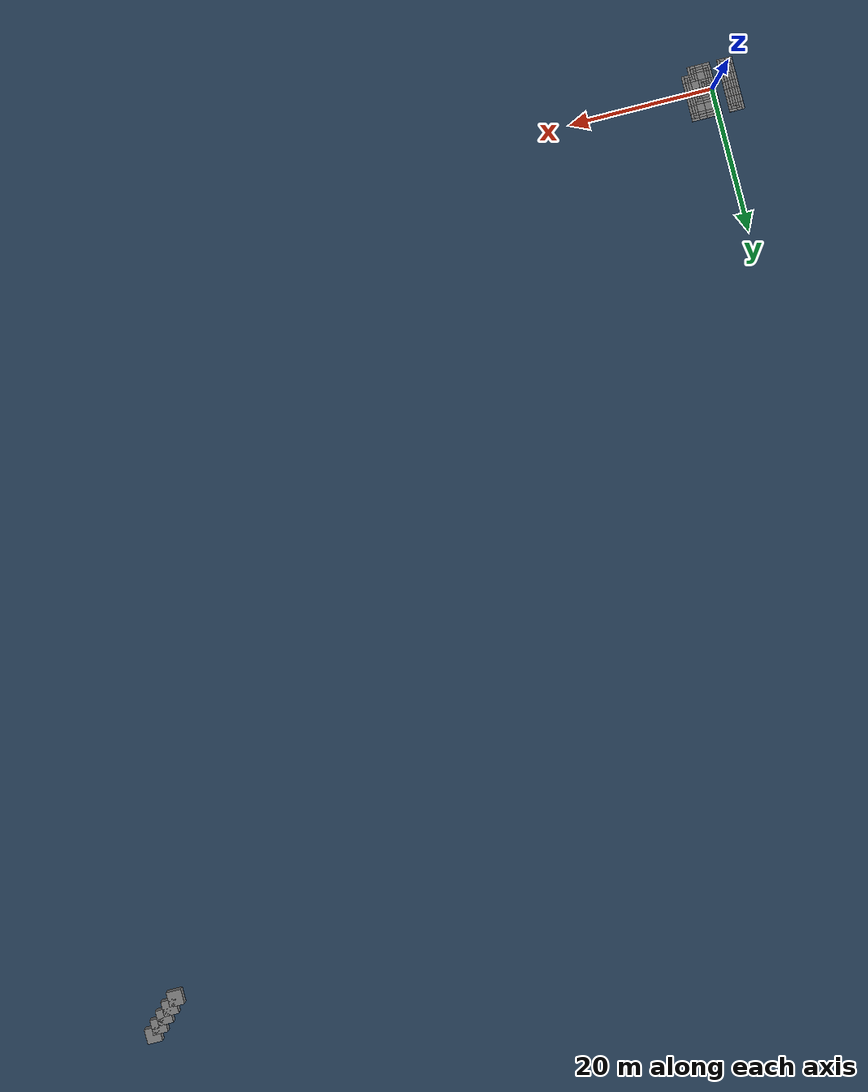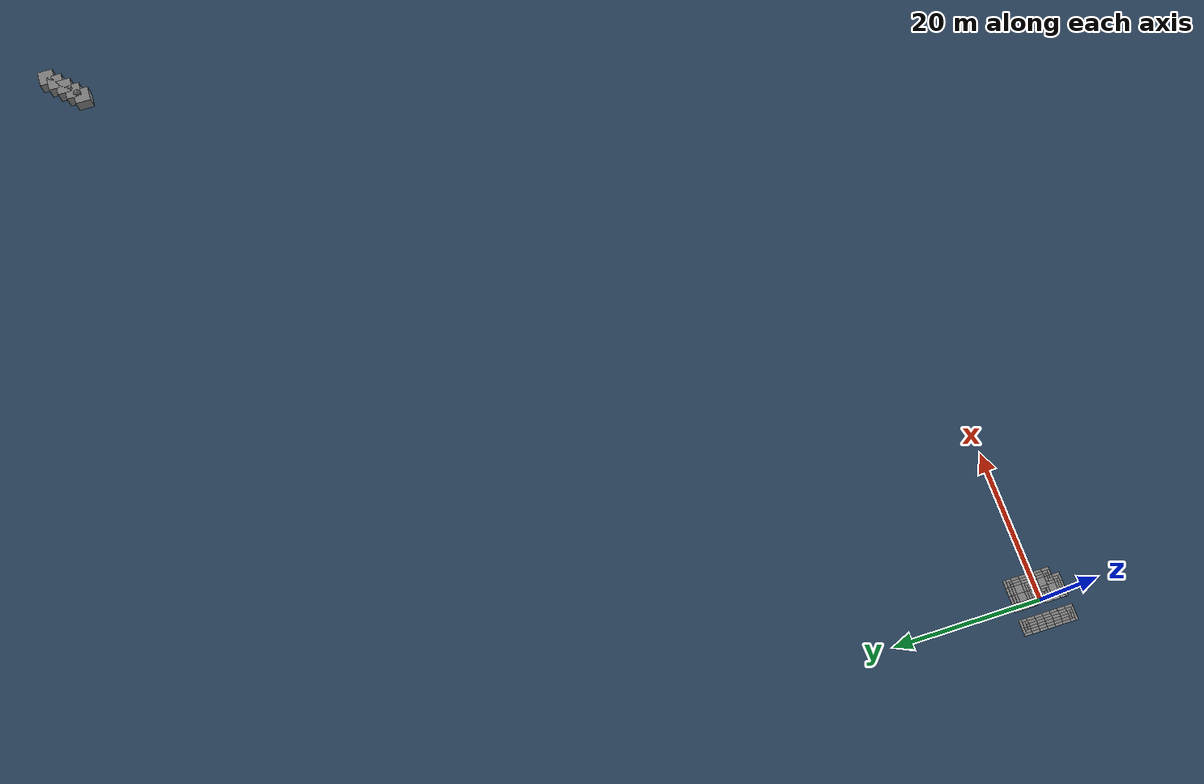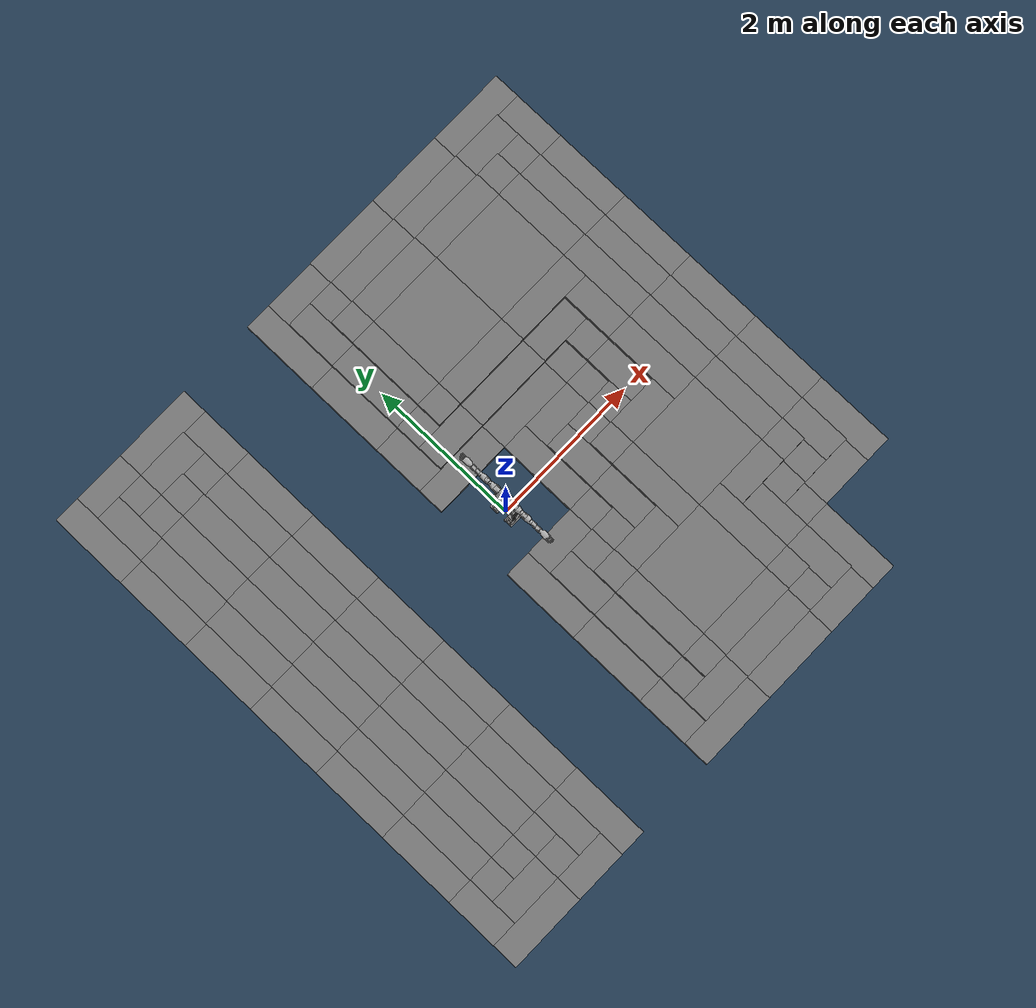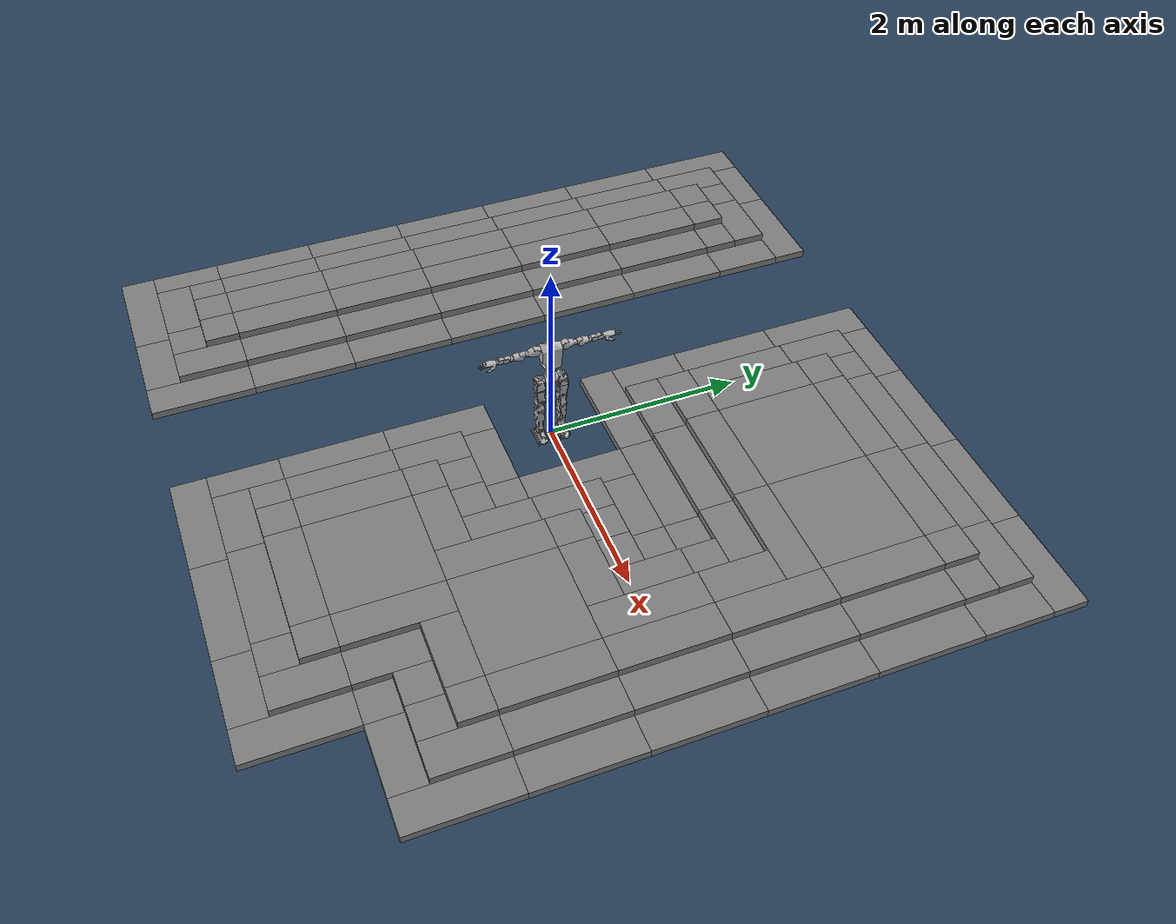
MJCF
<mujoco model="converted_robot scene">
  <include file="robot.xml" />
  <statistic center="0 0 1" extent="1.8" />

  <option timestep="0.001" iterations="100" solver="Newton" tolerance="1e-10">
    <flag warmstart="enable" contact="enable" />
  </option>

  <size nconmax="500" njmax="1000" />

  <keyframe>
    <key name="home" qpos="0 0 0.665 1 0 0 0                0 0 0                0 1.30 0 0 0 0 0 0                0 1.30 0 0 0 0 0 0                -0.707 0.062 -0.0553 -1.17 -0.458 0.0829                0.706 -0.0633 0.054 1.16 0.451 -0.0835" ctrl="0 0 0 0 0 0                0 0 0 0 0 0                0 0 0                0 0 0 0 0 0 0 0                0 0 0 0 0 0 0 0" />
  </keyframe>

  <visual>
    <headlight diffuse="0.6 0.6 0.6" ambient="0.3 0.3 0.3" specular="0 0 0" />
    <rgba haze="0.15 0.25 0.35 1" />
    <global azimuth="160" elevation="-20" />
  </visual>

  <asset>
    <texture type="skybox" builtin="gradient" rgb1="0.3 0.5 0.7" rgb2="0 0 0" width="512" height="3072" />
    <texture type="2d" name="groundplane" builtin="checker" mark="edge" rgb1="0.2 0.3 0.4" rgb2="0.1 0.2 0.3" markrgb="0.8 0.8 0.8" width="300" height="300" />
    <material name="groundplane" texture="groundplane" texuniform="true" texrepeat="5 5" reflectance="0.2" />
  </asset>

  <worldbody>
    <light pos="0 0 3.5" dir="0 0 -1" directional="true" />

    <geom name="floor" pos="0 0 0" size="0 0 0.05" type="plane" material="groundplane" contype="2" conaffinity="1" />
  <body pos="-2.7999999999999994 -2.7999999999999994 0.12" quat="0.7071067811865476 0.0 0.0 -0.7071067811865475" name="box_V4mo4"><geom type="box" size="0.175 0.175 0.12" contype="2" conaffinity="1" /></body><body pos="-2.9749999999999996 -3.1499999999999995 0.07999999999999999" quat="0.7071067811865476 0.0 0.0 -0.7071067811865475" name="box_vYk3Z"><geom type="box" size="0.175 0.35 0.07999999999999999" contype="2" conaffinity="1" /></body><body pos="-3.1499999999999995 -3.4999999999999996 0.03999999999999999" quat="0.7071067811865476 0.0 0.0 -0.7071067811865475" name="box_Kfs9x"><geom type="box" size="0.175 0.5249999999999999 0.03999999999999999" contype="2" conaffinity="1" /></body><body pos="-3.1499999999999995 -2.7999999999999994 0.07999999999999999" quat="1.0 0.0 0.0 0.0" name="box_ktW2B"><geom type="box" size="0.175 0.175 0.07999999999999999" contype="2" conaffinity="1" /></body><body pos="-3.4999999999999996 -2.9749999999999996 0.03999999999999999" quat="1.0 0.0 0.0 0.0" name="box_s9Wl7"><geom type="box" size="0.175 0.35 0.03999999999999999" contype="2" conaffinity="1" /></body><body pos="-3.4999999999999996 -2.0999999999999996 0.04" quat="1.0 0.0 0.0 0.0" name="box_LQZNL"><geom type="box" size="0.175 0.5249999999999999 0.04" contype="2" conaffinity="1" /></body><body pos="-3.1499999999999995 -2.0999999999999996 0.08" quat="1.0 0.0 0.0 0.0" name="box_v3tqq"><geom type="box" size="0.175 0.5249999999999999 0.08" contype="2" conaffinity="1" /></body><body pos="-2.7999999999999994 -2.0999999999999996 0.12" quat="1.0 0.0 0.0 0.0" name="box_Rq3DJ"><geom type="box" size="0.175 0.5249999999999999 0.12" contype="2" conaffinity="1" /></body><body pos="-3.4999999999999996 -1.0499999999999998 0.04" quat="1.0 0.0 0.0 0.0" name="box_BaevX"><geom type="box" size="0.175 0.5249999999999999 0.04" contype="2" conaffinity="1" /></body><body pos="-3.1499999999999995 -1.0499999999999998 0.08" quat="1.0 0.0 0.0 0.0" name="box_1OQDj"><geom type="box" size="0.175 0.5249999999999999 0.08" contype="2" conaffinity="1" /></body><body pos="-2.7999999999999994 -1.0499999999999998 0.12" quat="1.0 0.0 0.0 0.0" name="box_JVEAd"><geom type="box" size="0.175 0.5249999999999999 0.12" contype="2" conaffinity="1" /></body><body pos="-3.4999999999999996 0.0 0.04" quat="1.0 0.0 0.0 0.0" name="box_cbgC6"><geom type="box" size="0.175 0.5249999999999999 0.04" contype="2" conaffinity="1" /></body><body pos="-3.1499999999999995 0.0 0.08" quat="1.0 0.0 0.0 0.0" name="box_eWTiw"><geom type="box" size="0.175 0.5249999999999999 0.08" contype="2" conaffinity="1" /></body><body pos="-2.7999999999999994 0.0 0.12" quat="1.0 0.0 0.0 0.0" name="box_sr5d0"><geom type="box" size="0.175 0.5249999999999999 0.12" contype="2" conaffinity="1" /></body><body pos="-3.4999999999999996 1.0499999999999998 0.04" quat="1.0 0.0 0.0 0.0" name="box_4Jl46"><geom type="box" size="0.175 0.5249999999999999 0.04" contype="2" conaffinity="1" /></body><body pos="-3.1499999999999995 1.0499999999999998 0.08" quat="1.0 0.0 0.0 0.0" name="box_FdBU7"><geom type="box" size="0.175 0.5249999999999999 0.08" contype="2" conaffinity="1" /></body><body pos="-2.7999999999999994 1.0499999999999998 0.12" quat="1.0 0.0 0.0 0.0" name="box_NwZWy"><geom type="box" size="0.175 0.5249999999999999 0.12" contype="2" conaffinity="1" /></body><body pos="-3.4999999999999996 2.0999999999999996 0.04" quat="1.0 0.0 0.0 0.0" name="box_eJHX6"><geom type="box" size="0.175 0.5249999999999999 0.04" contype="2" conaffinity="1" /></body><body pos="-3.1499999999999995 2.0999999999999996 0.08" quat="1.0 0.0 0.0 0.0" name="box_4COW5"><geom type="box" size="0.175 0.5249999999999999 0.08" contype="2" conaffinity="1" /></body><body pos="-2.7999999999999994 2.0999999999999996 0.12" quat="1.0 0.0 0.0 0.0" name="box_ylptV"><geom type="box" size="0.175 0.5249999999999999 0.12" contype="2" conaffinity="1" /></body><body pos="-2.7999999999999994 2.7999999999999994 0.12" quat="6.123233995736766e-17 0.0 0.0 1.0" name="box_21vIJ"><geom type="box" size="0.175 0.175 0.12" contype="2" conaffinity="1" /></body><body pos="-3.1499999999999995 2.9749999999999996 0.07999999999999999" quat="6.123233995736766e-17 0.0 0.0 1.0" name="box_FD7hT"><geom type="box" size="0.175 0.35 0.07999999999999999" contype="2" conaffinity="1" /></body><body pos="-3.4999999999999996 3.1499999999999995 0.03999999999999999" quat="6.123233995736766e-17 0.0 0.0 1.0" name="box_ULNKZ"><geom type="box" size="0.175 0.5249999999999999 0.03999999999999999" contype="2" conaffinity="1" /></body><body pos="-2.7999999999999994 3.1499999999999995 0.07999999999999999" quat="-0.7071067811865475 -0.0 0.0 0.7071067811865476" name="box_GirD6"><geom type="box" size="0.175 0.175 0.07999999999999999" contype="2" conaffinity="1" /></body><body pos="-2.9749999999999996 3.4999999999999996 0.03999999999999999" quat="-0.7071067811865475 -0.0 0.0 0.7071067811865476" name="box_fcYUa"><geom type="box" size="0.175 0.35 0.03999999999999999" contype="2" conaffinity="1" /></body><body pos="-2.4499999999999997 -2.7999999999999994 0.12" quat="1.0 0.0 0.0 0.0" name="box_CshoT"><geom type="box" size="0.175 0.175 0.12" contype="2" conaffinity="1" /></body><body pos="-2.0999999999999996 -2.9749999999999996 0.07999999999999999" quat="1.0 0.0 0.0 0.0" name="box_Q1pGv"><geom type="box" size="0.175 0.35 0.07999999999999999" contype="2" conaffinity="1" /></body><body pos="-1.7499999999999996 -3.1499999999999995 0.03999999999999999" quat="1.0 0.0 0.0 0.0" name="box_6qOV8"><geom type="box" size="0.175 0.5249999999999999 0.03999999999999999" contype="2" conaffinity="1" /></body><body pos="-2.4499999999999997 -3.1499999999999995 0.07999999999999999" quat="0.7071067811865476 0.0 0.0 0.7071067811865475" name="box_9UYvp"><geom type="box" size="0.175 0.175 0.07999999999999999" contype="2" conaffinity="1" /></body><body pos="-2.2749999999999995 -3.4999999999999996 0.03999999999999999" quat="0.7071067811865476 0.0 0.0 0.7071067811865475" name="box_ELSCU"><geom type="box" size="0.175 0.35 0.03999999999999999" contype="2" conaffinity="1" /></body><body pos="-1.7499999999999998 -2.0999999999999996 0.04" quat="6.123233995736766e-17 0.0 0.0 1.0" name="box_pRboy"><geom type="box" size="0.175 0.5249999999999999 0.04" contype="2" conaffinity="1" /></body><body pos="-2.0999999999999996 -2.0999999999999996 0.08" quat="6.123233995736766e-17 0.0 0.0 1.0" name="box_hybFf"><geom type="box" size="0.175 0.5249999999999999 0.08" contype="2" conaffinity="1" /></body><body pos="-2.4499999999999997 -2.0999999999999996 0.12" quat="6.123233995736766e-17 0.0 0.0 1.0" name="box_O0mvc"><geom type="box" size="0.175 0.5249999999999999 0.12" contype="2" conaffinity="1" /></body><body pos="-1.7499999999999998 -1.0499999999999998 0.04" quat="6.123233995736766e-17 0.0 0.0 1.0" name="box_m7t7D"><geom type="box" size="0.175 0.5249999999999999 0.04" contype="2" conaffinity="1" /></body><body pos="-2.0999999999999996 -1.0499999999999998 0.08" quat="6.123233995736766e-17 0.0 0.0 1.0" name="box_HTPrm"><geom type="box" size="0.175 0.5249999999999999 0.08" contype="2" conaffinity="1" /></body><body pos="-2.4499999999999997 -1.0499999999999998 0.12" quat="6.123233995736766e-17 0.0 0.0 1.0" name="box_eQMty"><geom type="box" size="0.175 0.5249999999999999 0.12" contype="2" conaffinity="1" /></body><body pos="-1.7499999999999998 -4.2862637970157354e-17 0.04" quat="6.123233995736766e-17 0.0 0.0 1.0" name="box_0WJj3"><geom type="box" size="0.175 0.5249999999999999 0.04" contype="2" conaffinity="1" /></body><body pos="-2.0999999999999996 0.0 0.08" quat="6.123233995736766e-17 0.0 0.0 1.0" name="box_L7iiV"><geom type="box" size="0.175 0.5249999999999999 0.08" contype="2" conaffinity="1" /></body><body pos="-2.4499999999999997 4.286263797015736e-17 0.12" quat="6.123233995736766e-17 0.0 0.0 1.0" name="box_dm8KL"><geom type="box" size="0.175 0.5249999999999999 0.12" contype="2" conaffinity="1" /></body><body pos="-1.7499999999999998 1.0499999999999998 0.04" quat="6.123233995736766e-17 0.0 0.0 1.0" name="box_93S56"><geom type="box" size="0.175 0.5249999999999999 0.04" contype="2" conaffinity="1" /></body><body pos="-2.0999999999999996 1.0499999999999998 0.08" quat="6.123233995736766e-17 0.0 0.0 1.0" name="box_ne36Q"><geom type="box" size="0.175 0.5249999999999999 0.08" contype="2" conaffinity="1" /></body><body pos="-2.4499999999999997 1.0499999999999998 0.12" quat="6.123233995736766e-17 0.0 0.0 1.0" name="box_lG1Kk"><geom type="box" size="0.175 0.5249999999999999 0.12" contype="2" conaffinity="1" /></body><body pos="-1.7499999999999998 2.0999999999999996 0.04" quat="6.123233995736766e-17 0.0 0.0 1.0" name="box_LS9tp"><geom type="box" size="0.175 0.5249999999999999 0.04" contype="2" conaffinity="1" /></body><body pos="-2.0999999999999996 2.0999999999999996 0.08" quat="6.123233995736766e-17 0.0 0.0 1.0" name="box_nnBGS"><geom type="box" size="0.175 0.5249999999999999 0.08" contype="2" conaffinity="1" /></body><body pos="-2.4499999999999997 2.0999999999999996 0.12" quat="6.123233995736766e-17 0.0 0.0 1.0" name="box_bMdOH"><geom type="box" size="0.175 0.5249999999999999 0.12" contype="2" conaffinity="1" /></body><body pos="-2.4499999999999997 2.7999999999999994 0.12" quat="0.7071067811865476 0.0 0.0 0.7071067811865475" name="box_zzBhW"><geom type="box" size="0.175 0.175 0.12" contype="2" conaffinity="1" /></body><body pos="-2.2749999999999995 3.1499999999999995 0.07999999999999999" quat="0.7071067811865476 0.0 0.0 0.7071067811865475" name="box_51SOK"><geom type="box" size="0.175 0.35 0.07999999999999999" contype="2" conaffinity="1" /></body><body pos="-2.0999999999999996 3.4999999999999996 0.03999999999999999" quat="0.7071067811865476 0.0 0.0 0.7071067811865475" name="box_KrVMM"><geom type="box" size="0.175 0.5249999999999999 0.03999999999999999" contype="2" conaffinity="1" /></body><body pos="-2.0999999999999996 2.7999999999999994 0.07999999999999999" quat="6.123233995736766e-17 0.0 0.0 1.0" name="box_6gUWh"><geom type="box" size="0.175 0.175 0.07999999999999999" contype="2" conaffinity="1" /></body><body pos="-1.7499999999999996 2.9749999999999996 0.03999999999999999" quat="6.123233995736766e-17 0.0 0.0 1.0" name="box_IzdDW"><geom type="box" size="0.175 0.35 0.03999999999999999" contype="2" conaffinity="1" /></body><body pos="0.3499999999999999 -2.7999999999999994 0.12" quat="0.7071067811865476 0.0 0.0 -0.7071067811865475" name="box_oMdSc"><geom type="box" size="0.175 0.175 0.12" contype="2" conaffinity="1" /></body><body pos="0.17499999999999993 -3.1499999999999995 0.07999999999999999" quat="0.7071067811865476 0.0 0.0 -0.7071067811865475" name="box_34S06"><geom type="box" size="0.175 0.35 0.07999999999999999" contype="2" conaffinity="1" /></body><body pos="-3.4079832246179144e-17 -3.4999999999999996 0.03999999999999999" quat="0.7071067811865476 0.0 0.0 -0.7071067811865475" name="box_Zq0So"><geom type="box" size="0.175 0.5249999999999999 0.03999999999999999" contype="2" conaffinity="1" /></body><body pos="-5.551115123125783e-17 -2.7999999999999994 0.07999999999999999" quat="1.0 0.0 0.0 0.0" name="box_105jY"><geom type="box" size="0.175 0.175 0.07999999999999999" contype="2" conaffinity="1" /></body><body pos="-0.35000000000000003 -2.9749999999999996 0.03999999999999999" quat="1.0 0.0 0.0 0.0" name="box_tBWss"><geom type="box" size="0.175 0.35 0.03999999999999999" contype="2" conaffinity="1" /></body><body pos="-0.3499999999999999 -2.0999999999999996 0.04" quat="1.0 0.0 0.0 0.0" name="box_DyheJ"><geom type="box" size="0.175 0.5249999999999999 0.04" contype="2" conaffinity="1" /></body><body pos="0.0 -2.0999999999999996 0.08" quat="1.0 0.0 0.0 0.0" name="box_llb5Q"><geom type="box" size="0.175 0.5249999999999999 0.08" contype="2" conaffinity="1" /></body><body pos="0.35 -2.0999999999999996 0.12" quat="1.0 0.0 0.0 0.0" name="box_bhpGW"><geom type="box" size="0.175 0.5249999999999999 0.12" contype="2" conaffinity="1" /></body><body pos="0.3499999999999999 -1.4 0.12" quat="6.123233995736766e-17 0.0 0.0 1.0" name="box_meVMJ"><geom type="box" size="0.175 0.175 0.12" contype="2" conaffinity="1" /></body><body pos="-2.1431318985078674e-17 -1.2249999999999996 0.07999999999999999" quat="6.123233995736766e-17 0.0 0.0 1.0" name="box_U3GEh"><geom type="box" size="0.175 0.35 0.07999999999999999" contype="2" conaffinity="1" /></body><body pos="-0.35 -1.0499999999999998 0.03999999999999999" quat="6.123233995736766e-17 0.0 0.0 1.0" name="box_hwhco"><geom type="box" size="0.175 0.5249999999999999 0.03999999999999999" contype="2" conaffinity="1" /></body><body pos="0.3499999999999999 -1.0499999999999998 0.07999999999999999" quat="-0.7071067811865475 -0.0 0.0 0.7071067811865476" name="box_ETHsi"><geom type="box" size="0.175 0.175 0.07999999999999999" contype="2" conaffinity="1" /></body><body pos="0.175 -0.6999999999999998 0.03999999999999999" quat="-0.7071067811865475 -0.0 0.0 0.7071067811865476" name="box_j19jo"><geom type="box" size="0.175 0.35 0.03999999999999999" contype="2" conaffinity="1" /></body><body pos="0.3499999999999999 1.4 0.12" quat="0.7071067811865476 0.0 0.0 -0.7071067811865475" name="box_vmHop"><geom type="box" size="0.175 0.175 0.12" contype="2" conaffinity="1" /></body><body pos="0.17499999999999993 1.0499999999999998 0.07999999999999999" quat="0.7071067811865476 0.0 0.0 -0.7071067811865475" name="box_ho4aF"><geom type="box" size="0.175 0.35 0.07999999999999999" contype="2" conaffinity="1" /></body><body pos="-3.4079832246179144e-17 0.6999999999999998 0.03999999999999999" quat="0.7071067811865476 0.0 0.0 -0.7071067811865475" name="box_7TwJf"><geom type="box" size="0.175 0.5249999999999999 0.03999999999999999" contype="2" conaffinity="1" /></body><body pos="-5.551115123125783e-17 1.3999999999999997 0.07999999999999999" quat="1.0 0.0 0.0 0.0" name="box_tW0rf"><geom type="box" size="0.175 0.175 0.07999999999999999" contype="2" conaffinity="1" /></body><body pos="-0.35000000000000003 1.2249999999999996 0.03999999999999999" quat="1.0 0.0 0.0 0.0" name="box_gGuf9"><geom type="box" size="0.175 0.35 0.03999999999999999" contype="2" conaffinity="1" /></body><body pos="-0.3499999999999999 2.0999999999999996 0.04" quat="1.0 0.0 0.0 0.0" name="box_MFRqi"><geom type="box" size="0.175 0.5249999999999999 0.04" contype="2" conaffinity="1" /></body><body pos="0.0 2.0999999999999996 0.08" quat="1.0 0.0 0.0 0.0" name="box_F2LNs"><geom type="box" size="0.175 0.5249999999999999 0.08" contype="2" conaffinity="1" /></body><body pos="0.35 2.0999999999999996 0.12" quat="1.0 0.0 0.0 0.0" name="box_4qiGV"><geom type="box" size="0.175 0.5249999999999999 0.12" contype="2" conaffinity="1" /></body><body pos="0.3499999999999999 2.7999999999999994 0.12" quat="6.123233995736766e-17 0.0 0.0 1.0" name="box_SSVgU"><geom type="box" size="0.175 0.175 0.12" contype="2" conaffinity="1" /></body><body pos="-2.1431318985078674e-17 2.9749999999999996 0.07999999999999999" quat="6.123233995736766e-17 0.0 0.0 1.0" name="box_4pBKM"><geom type="box" size="0.175 0.35 0.07999999999999999" contype="2" conaffinity="1" /></body><body pos="-0.35 3.1499999999999995 0.03999999999999999" quat="6.123233995736766e-17 0.0 0.0 1.0" name="box_fcWz5"><geom type="box" size="0.175 0.5249999999999999 0.03999999999999999" contype="2" conaffinity="1" /></body><body pos="0.3499999999999999 3.1499999999999995 0.07999999999999999" quat="-0.7071067811865475 -0.0 0.0 0.7071067811865476" name="box_UcgL8"><geom type="box" size="0.175 0.175 0.07999999999999999" contype="2" conaffinity="1" /></body><body pos="0.175 3.4999999999999996 0.03999999999999999" quat="-0.7071067811865475 -0.0 0.0 0.7071067811865476" name="box_5VnHT"><geom type="box" size="0.175 0.35 0.03999999999999999" contype="2" conaffinity="1" /></body><body pos="1.0499999999999998 -3.4999999999999996 0.04" quat="0.7071067811865476 0.0 0.0 0.7071067811865475" name="box_eiYkG"><geom type="box" size="0.175 0.5249999999999999 0.04" contype="2" conaffinity="1" /></body><body pos="1.0499999999999998 -3.1499999999999995 0.08" quat="0.7071067811865476 0.0 0.0 0.7071067811865475" name="box_IWIHy"><geom type="box" size="0.175 0.5249999999999999 0.08" contype="2" conaffinity="1" /></body><body pos="1.0499999999999998 -2.7999999999999994 0.12" quat="0.7071067811865476 0.0 0.0 0.7071067811865475" name="box_lkdiY"><geom type="box" size="0.175 0.5249999999999999 0.12" contype="2" conaffinity="1" /></body><body pos="1.0499999999999998 -2.0999999999999996 0.12" quat="1.0 0.0 0.0 0.0" name="box_afQgK"><geom type="box" size="0.5249999999999999 0.5249999999999999 0.12" contype="2" conaffinity="1" /></body><body pos="0.6999999999999998 -0.7 0.04" quat="1.0 0.0 0.0 0.0" name="box_6SVm8"><geom type="box" size="0.175 0.175 0.04" contype="2" conaffinity="1" /></body><body pos="1.0499999999999998 -0.8749999999999999 0.08" quat="1.0 0.0 0.0 0.0" name="box_rF2Pt"><geom type="box" size="0.175 0.35 0.08" contype="2" conaffinity="1" /></body><body pos="1.4 -1.0499999999999998 0.12" quat="1.0 0.0 0.0 0.0" name="box_G1TzB"><geom type="box" size="0.175 0.5249999999999999 0.12" contype="2" conaffinity="1" /></body><body pos="0.7 -1.0499999999999998 0.08" quat="0.7071067811865476 0.0 0.0 0.7071067811865475" name="box_xTiHA"><geom type="box" size="0.175 0.175 0.08" contype="2" conaffinity="1" /></body><body pos="0.8749999999999999 -1.4 0.12" quat="0.7071067811865476 0.0 0.0 0.7071067811865475" name="box_CrvB3"><geom type="box" size="0.175 0.35 0.12" contype="2" conaffinity="1" /></body><body pos="1.3999999999999997 -0.35 0.12" quat="6.123233995736766e-17 0.0 0.0 1.0" name="box_r99rC"><geom type="box" size="0.175 0.175 0.12" contype="2" conaffinity="1" /></body><body pos="1.0499999999999998 -0.17499999999999993 0.07999999999999999" quat="6.123233995736766e-17 0.0 0.0 1.0" name="box_AWd9O"><geom type="box" size="0.175 0.35 0.07999999999999999" contype="2" conaffinity="1" /></body><body pos="0.6999999999999998 9.837378920141519e-17 0.03999999999999999" quat="6.123233995736766e-17 0.0 0.0 1.0" name="box_5ruSL"><geom type="box" size="0.175 0.5249999999999999 0.03999999999999999" contype="2" conaffinity="1" /></body><body pos="1.3999999999999997 -8.782805723978197e-18 0.07999999999999999" quat="-0.7071067811865475 -0.0 0.0 0.7071067811865476" name="box_ZY8Cz"><geom type="box" size="0.175 0.175 0.07999999999999999" contype="2" conaffinity="1" /></body><body pos="1.2249999999999999 0.35 0.03999999999999999" quat="-0.7071067811865475 -0.0 0.0 0.7071067811865476" name="box_wqp3g"><geom type="box" size="0.175 0.35 0.03999999999999999" contype="2" conaffinity="1" /></body><body pos="1.0499999999999998 0.7 0.04" quat="0.7071067811865476 0.0 0.0 0.7071067811865475" name="box_KZify"><geom type="box" size="0.175 0.5249999999999999 0.04" contype="2" conaffinity="1" /></body><body pos="1.0499999999999998 1.0499999999999998 0.08" quat="0.7071067811865476 0.0 0.0 0.7071067811865475" name="box_236zi"><geom type="box" size="0.175 0.5249999999999999 0.08" contype="2" conaffinity="1" /></body><body pos="1.0499999999999998 1.4 0.12" quat="0.7071067811865476 0.0 0.0 0.7071067811865475" name="box_JHSTe"><geom type="box" size="0.175 0.5249999999999999 0.12" contype="2" conaffinity="1" /></body><body pos="1.0499999999999998 2.0999999999999996 0.12" quat="1.0 0.0 0.0 0.0" name="box_RUphS"><geom type="box" size="0.5249999999999999 0.5249999999999999 0.12" contype="2" conaffinity="1" /></body><body pos="1.0499999999999998 3.4999999999999996 0.04" quat="0.7071067811865476 0.0 0.0 -0.7071067811865475" name="box_oTW5L"><geom type="box" size="0.175 0.5249999999999999 0.04" contype="2" conaffinity="1" /></body><body pos="1.0499999999999998 3.1499999999999995 0.08" quat="0.7071067811865476 0.0 0.0 -0.7071067811865475" name="box_H7YZW"><geom type="box" size="0.175 0.5249999999999999 0.08" contype="2" conaffinity="1" /></body><body pos="1.0499999999999998 2.7999999999999994 0.12" quat="0.7071067811865476 0.0 0.0 -0.7071067811865475" name="box_Vsrlf"><geom type="box" size="0.175 0.5249999999999999 0.12" contype="2" conaffinity="1" /></body><body pos="1.7499999999999996 -2.7999999999999994 0.12" quat="1.0 0.0 0.0 0.0" name="box_aaBCp"><geom type="box" size="0.175 0.175 0.12" contype="2" conaffinity="1" /></body><body pos="2.0999999999999996 -2.9749999999999996 0.07999999999999999" quat="1.0 0.0 0.0 0.0" name="box_czRX9"><geom type="box" size="0.175 0.35 0.07999999999999999" contype="2" conaffinity="1" /></body><body pos="2.4499999999999997 -3.1499999999999995 0.03999999999999999" quat="1.0 0.0 0.0 0.0" name="box_s2C0o"><geom type="box" size="0.175 0.5249999999999999 0.03999999999999999" contype="2" conaffinity="1" /></body><body pos="1.7499999999999998 -3.1499999999999995 0.07999999999999999" quat="0.7071067811865476 0.0 0.0 0.7071067811865475" name="box_8WJij"><geom type="box" size="0.175 0.175 0.07999999999999999" contype="2" conaffinity="1" /></body><body pos="1.9249999999999996 -3.4999999999999996 0.03999999999999999" quat="0.7071067811865476 0.0 0.0 0.7071067811865475" name="box_UfMQs"><geom type="box" size="0.175 0.35 0.03999999999999999" contype="2" conaffinity="1" /></body><body pos="2.4499999999999997 -2.4499999999999997 0.04" quat="6.123233995736766e-17 0.0 0.0 1.0" name="box_Mc7yp"><geom type="box" size="0.175 0.175 0.04" contype="2" conaffinity="1" /></body><body pos="2.0999999999999996 -2.2749999999999995 0.08" quat="6.123233995736766e-17 0.0 0.0 1.0" name="box_gxN9P"><geom type="box" size="0.175 0.35 0.08" contype="2" conaffinity="1" /></body><body pos="1.7499999999999996 -2.0999999999999996 0.12" quat="6.123233995736766e-17 0.0 0.0 1.0" name="box_WrnSI"><geom type="box" size="0.175 0.5249999999999999 0.12" contype="2" conaffinity="1" /></body><body pos="2.4499999999999997 -2.0999999999999996 0.08" quat="-0.7071067811865475 -0.0 0.0 0.7071067811865476" name="box_gF0p3"><geom type="box" size="0.175 0.175 0.08" contype="2" conaffinity="1" /></body><body pos="2.2749999999999995 -1.7499999999999996 0.12" quat="-0.7071067811865475 -0.0 0.0 0.7071067811865476" name="box_BrTbi"><geom type="box" size="0.175 0.35 0.12" contype="2" conaffinity="1" /></body><body pos="2.0999999999999996 -1.0499999999999998 0.12" quat="1.0 0.0 0.0 0.0" name="box_MYzPO"><geom type="box" size="0.5249999999999999 0.5249999999999999 0.12" contype="2" conaffinity="1" /></body><body pos="1.7499999999999996 0.3499999999999999 0.04" quat="1.0 0.0 0.0 0.0" name="box_uzrX0"><geom type="box" size="0.175 0.175 0.04" contype="2" conaffinity="1" /></body><body pos="2.0999999999999996 0.17499999999999993 0.08" quat="1.0 0.0 0.0 0.0" name="box_AeAPV"><geom type="box" size="0.175 0.35 0.08" contype="2" conaffinity="1" /></body><body pos="2.4499999999999997 -5.551115123125783e-17 0.12" quat="1.0 0.0 0.0 0.0" name="box_4eXNf"><geom type="box" size="0.175 0.5249999999999999 0.12" contype="2" conaffinity="1" /></body><body pos="1.7499999999999998 -3.407983224617915e-17 0.08" quat="0.7071067811865476 0.0 0.0 0.7071067811865475" name="box_B0LrS"><geom type="box" size="0.175 0.175 0.08" contype="2" conaffinity="1" /></body><body pos="1.9249999999999996 -0.35000000000000003 0.12" quat="0.7071067811865476 0.0 0.0 0.7071067811865475" name="box_TbaiX"><geom type="box" size="0.175 0.35 0.12" contype="2" conaffinity="1" /></body><body pos="1.7499999999999998 0.6999999999999998 0.04" quat="0.7071067811865476 0.0 0.0 0.7071067811865475" name="box_qT8CH"><geom type="box" size="0.175 0.175 0.04" contype="2" conaffinity="1" /></body><body pos="1.9249999999999998 1.0499999999999998 0.08" quat="0.7071067811865476 0.0 0.0 0.7071067811865475" name="box_QcDnS"><geom type="box" size="0.175 0.35 0.08" contype="2" conaffinity="1" /></body><body pos="2.0999999999999996 1.4 0.12" quat="0.7071067811865476 0.0 0.0 0.7071067811865475" name="box_3yWNl"><geom type="box" size="0.175 0.5249999999999999 0.12" contype="2" conaffinity="1" /></body><body pos="2.0999999999999996 0.7 0.08" quat="6.123233995736766e-17 0.0 0.0 1.0" name="box_ZBqS9"><geom type="box" size="0.175 0.175 0.08" contype="2" conaffinity="1" /></body><body pos="2.4499999999999997 0.8749999999999998 0.12" quat="6.123233995736766e-17 0.0 0.0 1.0" name="box_AGRDR"><geom type="box" size="0.175 0.35 0.12" contype="2" conaffinity="1" /></body><body pos="2.0999999999999996 2.0999999999999996 0.12" quat="1.0 0.0 0.0 0.0" name="box_brFWV"><geom type="box" size="0.5249999999999999 0.5249999999999999 0.12" contype="2" conaffinity="1" /></body><body pos="2.0999999999999996 3.4999999999999996 0.04" quat="0.7071067811865476 0.0 0.0 -0.7071067811865475" name="box_k8zoR"><geom type="box" size="0.175 0.5249999999999999 0.04" contype="2" conaffinity="1" /></body><body pos="2.0999999999999996 3.1499999999999995 0.08" quat="0.7071067811865476 0.0 0.0 -0.7071067811865475" name="box_RVpKa"><geom type="box" size="0.175 0.5249999999999999 0.08" contype="2" conaffinity="1" /></body><body pos="2.0999999999999996 2.7999999999999994 0.12" quat="0.7071067811865476 0.0 0.0 -0.7071067811865475" name="box_iftrt"><geom type="box" size="0.175 0.5249999999999999 0.12" contype="2" conaffinity="1" /></body><body pos="2.7999999999999994 -1.7499999999999998 0.12" quat="1.0 0.0 0.0 0.0" name="box_yaUTq"><geom type="box" size="0.175 0.175 0.12" contype="2" conaffinity="1" /></body><body pos="3.1499999999999995 -1.9249999999999998 0.07999999999999999" quat="1.0 0.0 0.0 0.0" name="box_IxkT6"><geom type="box" size="0.175 0.35 0.07999999999999999" contype="2" conaffinity="1" /></body><body pos="3.4999999999999996 -2.0999999999999996 0.03999999999999999" quat="1.0 0.0 0.0 0.0" name="box_pMLIC"><geom type="box" size="0.175 0.5249999999999999 0.03999999999999999" contype="2" conaffinity="1" /></body><body pos="2.7999999999999994 -2.0999999999999996 0.07999999999999999" quat="0.7071067811865476 0.0 0.0 0.7071067811865475" name="box_kuzCn"><geom type="box" size="0.175 0.175 0.07999999999999999" contype="2" conaffinity="1" /></body><body pos="2.9749999999999996 -2.4499999999999997 0.03999999999999999" quat="0.7071067811865476 0.0 0.0 0.7071067811865475" name="box_96XZg"><geom type="box" size="0.175 0.35 0.03999999999999999" contype="2" conaffinity="1" /></body><body pos="3.4999999999999996 -1.0499999999999998 0.04" quat="6.123233995736766e-17 0.0 0.0 1.0" name="box_NuBtn"><geom type="box" size="0.175 0.5249999999999999 0.04" contype="2" conaffinity="1" /></body><body pos="3.1499999999999995 -1.0499999999999998 0.08" quat="6.123233995736766e-17 0.0 0.0 1.0" name="box_ClFsW"><geom type="box" size="0.175 0.5249999999999999 0.08" contype="2" conaffinity="1" /></body><body pos="2.7999999999999994 -1.0499999999999998 0.12" quat="6.123233995736766e-17 0.0 0.0 1.0" name="box_8fqaz"><geom type="box" size="0.175 0.5249999999999999 0.12" contype="2" conaffinity="1" /></body><body pos="3.4999999999999996 -4.2862637970157354e-17 0.04" quat="6.123233995736766e-17 0.0 0.0 1.0" name="box_bGAH4"><geom type="box" size="0.175 0.5249999999999999 0.04" contype="2" conaffinity="1" /></body><body pos="3.1499999999999995 0.0 0.08" quat="6.123233995736766e-17 0.0 0.0 1.0" name="box_gaHay"><geom type="box" size="0.175 0.5249999999999999 0.08" contype="2" conaffinity="1" /></body><body pos="2.7999999999999994 4.286263797015736e-17 0.12" quat="6.123233995736766e-17 0.0 0.0 1.0" name="box_E0fg9"><geom type="box" size="0.175 0.5249999999999999 0.12" contype="2" conaffinity="1" /></body><body pos="3.4999999999999996 1.0499999999999998 0.04" quat="6.123233995736766e-17 0.0 0.0 1.0" name="box_LInhQ"><geom type="box" size="0.175 0.5249999999999999 0.04" contype="2" conaffinity="1" /></body><body pos="3.1499999999999995 1.0499999999999998 0.08" quat="6.123233995736766e-17 0.0 0.0 1.0" name="box_2I5wm"><geom type="box" size="0.175 0.5249999999999999 0.08" contype="2" conaffinity="1" /></body><body pos="2.7999999999999994 1.0499999999999998 0.12" quat="6.123233995736766e-17 0.0 0.0 1.0" name="box_3wrjb"><geom type="box" size="0.175 0.5249999999999999 0.12" contype="2" conaffinity="1" /></body><body pos="3.4999999999999996 2.0999999999999996 0.04" quat="6.123233995736766e-17 0.0 0.0 1.0" name="box_RnOh2"><geom type="box" size="0.175 0.5249999999999999 0.04" contype="2" conaffinity="1" /></body><body pos="3.1499999999999995 2.0999999999999996 0.08" quat="6.123233995736766e-17 0.0 0.0 1.0" name="box_zZwgf"><geom type="box" size="0.175 0.5249999999999999 0.08" contype="2" conaffinity="1" /></body><body pos="2.7999999999999994 2.0999999999999996 0.12" quat="6.123233995736766e-17 0.0 0.0 1.0" name="box_He6dv"><geom type="box" size="0.175 0.5249999999999999 0.12" contype="2" conaffinity="1" /></body><body pos="2.7999999999999994 2.7999999999999994 0.12" quat="0.7071067811865476 0.0 0.0 0.7071067811865475" name="box_1zXU9"><geom type="box" size="0.175 0.175 0.12" contype="2" conaffinity="1" /></body><body pos="2.9749999999999996 3.1499999999999995 0.07999999999999999" quat="0.7071067811865476 0.0 0.0 0.7071067811865475" name="box_5MIzU"><geom type="box" size="0.175 0.35 0.07999999999999999" contype="2" conaffinity="1" /></body><body pos="3.1499999999999995 3.4999999999999996 0.03999999999999999" quat="0.7071067811865476 0.0 0.0 0.7071067811865475" name="box_A3USW"><geom type="box" size="0.175 0.5249999999999999 0.03999999999999999" contype="2" conaffinity="1" /></body><body pos="3.1499999999999995 2.7999999999999994 0.07999999999999999" quat="6.123233995736766e-17 0.0 0.0 1.0" name="box_VEmzV"><geom type="box" size="0.175 0.175 0.07999999999999999" contype="2" conaffinity="1" /></body><body pos="3.4999999999999996 2.9749999999999996 0.03999999999999999" quat="6.123233995736766e-17 0.0 0.0 1.0" name="box_e40ey"><geom type="box" size="0.175 0.35 0.03999999999999999" contype="2" conaffinity="1" /></body><body pos="100 100 10" quat="1.0 0.0 0.0 0.0" name="box_cJtFG"><geom type="box" size="1.0 1.0 1.0" contype="2" conaffinity="1" /></body><body pos="101 101 10" quat="1.0 0.0 0.0 0.0" name="box_3Xw8a"><geom type="box" size="1.0 1.0 1.0" contype="2" conaffinity="1" /></body><body pos="102 102 10" quat="1.0 0.0 0.0 0.0" name="box_MW3cD"><geom type="box" size="1.0 1.0 1.0" contype="2" conaffinity="1" /></body><body pos="103 103 10" quat="1.0 0.0 0.0 0.0" name="box_VsEA4"><geom type="box" size="1.0 1.0 1.0" contype="2" conaffinity="1" /></body><body pos="104 104 10" quat="1.0 0.0 0.0 0.0" name="box_kbC37"><geom type="box" size="1.0 1.0 1.0" contype="2" conaffinity="1" /></body></worldbody>

</mujoco>

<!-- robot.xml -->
<mujoco model="r2-1024">

  <compiler angle="radian" autolimits="true"/>

  <option iterations="2" ls_iterations="5" gravity="0.0 0.0 -9.81">
    <flag eulerdamp="disable" />
  </option>

  <statistic meansize="0.05"/>

  <default>
      <default class="r2">
        <joint damping="1.0" armature="0.1"/>
        <default class="visual">
            <geom type="mesh" contype="0" conaffinity="0" group="2" material="black"/>
        </default>
        <default class="r2foot">
          <site group="1" pos="0.014 0 -0.046" />
          <geom rgba="0.231373 0.380392 0.705882 1" />
        </default>
        <site size="0.01" rgba="0.5 0.5 0.5 0.3" group="4"/>
        <default class="collision">
          <geom group="1"/>
        </default>
      </default>
  </default>

  <worldbody>
    <body name="base_link" quat="1 0 0 0" pos="0 0 0.7536" childclass="r2">
      <freejoint/>
      <inertial pos="-0.0002 4e-05 -0.04522" quat="0.498303 0.499454 -0.500496 0.501741" mass="5"
        diaginertia="0.0490211 0.0445821 0.00824619"/>
      <geom name="base_link_visual" class="visual" mesh="base_link_base_link" material="default_material" />
      <body name="waist-yaw" pos="0 0 0.1015">
        <inertial pos="0.000838548932558386 1.9429471902685E-06 0.0186119972543407" mass="0.167524107737489" diaginertia="9.88251687847136e-05 0.000102644683208664 0.000183718897605441" />
        <joint name="waist-yaw" type="hinge" range="-2.35 2.35" axis="0 0 1" />
        <geom name="waist-yaw_visual" class="visual" mesh="waist-yaw_waist-yaw" material="default_material" />
        <body name="waist-roll" pos="0 0 0.0469999999999995">
          <inertial pos="1.97709520768918E-08 1.97091613064748E-08 2.31318830895555E-08" mass="0.0511904050675653" diaginertia="3.39482519018086e-06 5.66454429374261e-06 4.73575691209588e-06" />
          <joint name="waist-roll" type="hinge" range="-0.52 0.52" axis="-1 0 0" />
          <geom name="waist-roll_visual" class="visual" mesh="waist-roll_waist-roll" material="default_material" />
          <body name="waist-pitch">
            <inertial pos="0.00344100284916034 0.0033421324318141 0.178579205212244" mass="6.84868650679273" diaginertia="0.0455180072144121 0.0320278136152675 0.0239625384602924" />
            <joint name="waist-pitch" type="hinge" range="-0.52 0.52" axis="0 -0.999993041789322 0.00373046551240819" />
            <geom name="waist-pitch_visual" class="visual" mesh="waist-pitch_waist-pitch" material="default_material" />
            <body name="Rshoulder-pitch" pos="0.00124892699365971 -0.103096515714583 0.242383061761496">
              <inertial pos="1.19739327765281E-05 -0.037631766969166 0.00257001764547576" mass="0.351201296180657" diaginertia="0.000529028614216069 0.000352986817594136 0.000381088824596585" />
              <joint name="Rshoulder-pitch" type="hinge" range="-2.87 2.87" axis="0 0.999993041789322 -0.00373046551240969" />
              <geom name="Rshoulder-pitch_visual" class="visual" mesh="Rshoulder-pitch_Rshoulder-pitch" material="default_material" />
              <body name="Rshoulder-roll" pos="-0.00124892699365824 -0.0460005024348026 -4.88822667354949E-05">
                <inertial pos="-0.000812832414537328 -0.0271831429862336 0.00142268753344876" mass="0.901300574234884" diaginertia="0.000874742091802788 0.000766595366318081 0.00105432805094867" />
                <joint name="Rshoulder-roll" type="hinge" range="-1.34 2.79" axis="0.999986682697375 -1.92523928883499E-05 -0.00516081943538461" />
                <geom name="Rshoulder-roll_visual" class="visual" mesh="Rshoulder-roll_Rshoulder-roll" material="default_material" />
                <body name="Rarm-pitch" pos="0.00124892699365715 -0.0939985234157071 0.000571147438479858">
                  <inertial pos="-5.86523797540886E-05 -0.0480215847112014 -0.0115614509170335" mass="0.163656043089394" diaginertia="0.000205301785507928 0.000137025660099078 0.000154567593086099" />
                  <joint name="Rarm-pitch" type="hinge" range="-1.57 1.57" axis="0 0.999993041789322 -0.00373046551241809" />
                  <geom name="Rarm-pitch_visual" class="visual" mesh="Rarm-pitch_Rarm-pitch" material="default_material" />
                  <body name="Rarm-roll" pos="-0.00124892699365667 -0.0600749118698925 -0.019969050977966">
                    <inertial pos="0.00117500064437485 -0.0296883325386475 0.00611806709758506" mass="0.790024730889843" diaginertia="0.000626951373773776 0.000565474955147993 0.000724094109271216" />
                    <joint name="Rarm-roll" type="hinge" range="-2.09 2.09" axis="-0.999986682697375 1.92523928882734E-05 0.00516081943539328" />
                    <geom name="Rarm-roll_visual" class="visual" mesh="Rarm-roll_Rarm-roll" material="default_material" />
                    <body name="Rforearm-pitch" pos="0.00118699671361817 -0.0874688267955187 0.00851953486706497">
                      <inertial pos="-7.39438371644141E-12 -0.0332659563873272 0.000124095077057351" mass="0.0616964140219398" diaginertia="1.71013816255747e-05 1.4645711027657e-05 2.68440203486961e-05" />
                      <joint name="Rforearm-pitch" type="hinge" range="-1.57 1.57" axis="0 0.999993041789322 -0.00373046551242672" />
                      <geom name="Rforearm-pitch_visual" class="visual" mesh="Rforearm-pitch_Rforearm-pitch" material="default_material" />
                      <body name="Rforearm-yaw" pos="0 -0.0519996381730424 0.000193984206656894">
                        <inertial pos="-0.00144914299769784 -0.024023819187538 -0.00133242424970514" mass="0.286322539919696" diaginertia="0.000207156464271699 7.94674704834646e-05 0.000207083820030091" />
                        <joint name="Rforearm-yaw" type="hinge" range="-1.57 1.57" axis="0.00516085534561842 0.00373041583270884 0.999979724579362" />
                        <geom name="Rforearm-yaw_visual" class="visual" mesh="Rforearm-yaw_Rforearm-yaw" material="default_material" />
                        <body name="Rforearm-roll" pos="0 -0.0479996660058844 0.000179062344592917">
                          <inertial pos="-0.000432292829653728 -0.0218265392717949 -9.51317515698324E-05" mass="0.0776563326897135" diaginertia="2.75633138511378e-05 1.84792179561101e-05 1.89294300843364e-05" />
                          <joint name="Rforearm-roll" type="hinge" range="-2.09 2.09" axis="-0.999986682697376 1.92523927639293E-05 0.00516081943529982" />
                          <geom name="Rforearm-roll_visual" class="visual" mesh="Rforearm-roll_Rforearm-roll" material="default_material" />
                          <body name="Rwrist-pitch" pos="-0.000310603277652269 -0.0289997922319544 0.000109786488636632">
                            <inertial pos="0.000399588449917054 -0.099108422325107 0.00163681066572025" mass="0.0581113383823661" diaginertia="2.27805031940733e-05 1.16579826647684e-05 2.76365481980842e-05" />
                            <joint name="Rwrist-pitch" type="hinge" range="-1.57 1.57" axis="0 0.999993041789322 -0.00373046551231421" />
                            <geom name="Rwrist-pitch_visual" class="visual" mesh="Rwrist-pitch_Rwrist-pitch" material="default_material" />
                          </body>
                        </body>
                      </body>
                    </body>
                  </body>
                </body>
              </body>
            </body>
            <body name="Lshoulder-pitch" pos="0.00127140572076783 0.105918012627561 0.245887711508865">
              <inertial pos="-9.37455533417397E-06 0.0366339168984884 -0.00199140885891902" mass="0.351201337508422" diaginertia="0.000529028510877296 0.000353281271768694 0.000380794448638633" />
              <joint name="Lshoulder-pitch" type="hinge" range="-2.87 2.87" axis="0 -0.999993041789322 0.00373046551240926" />
              <geom name="Lshoulder-pitch_visual" class="visual" mesh="Lshoulder-pitch_Lshoulder-pitch" material="default_material" />
              <body name="Lshoulder-roll" pos="-2.24787271085117E-05 0.0449837042723494 -0.00445218798751273">
                <inertial pos="0.00207301104207318 0.0271920986739509 0.00097801408904552" mass="0.901300591228606" diaginertia="0.000874808646674644 0.000766264670712621 0.00105459222467771" />
                <joint name="Lshoulder-roll" type="hinge" range="-2.79 1.34" axis="-0.999986682697375 1.92523928881331E-05 0.00516081943538374" />
                <geom name="Lshoulder-roll_visual" class="visual" mesh="Lshoulder-roll_Lshoulder-roll" material="default_material" />
                <body name="Larm-pitch" pos="0 0.106999255471457 -0.000399159809829575">
                  <inertial pos="-6.25416723689237E-05 0.0349340834086484 -0.0118708978450517" mass="0.163656024444727" diaginertia="0.000205301678168692 0.000137463543125656 0.000154129771734942" />
                  <joint name="Larm-pitch" type="hinge" range="-1.57 1.57" axis="0 -0.999993041789322 0.00373046551243847" />
                  <geom name="Larm-pitch_visual" class="visual" mesh="Larm-pitch_Larm-pitch" material="default_material" />
                  <body name="Larm-roll" pos="-0.000103217106914702 0.0469250646474482 -0.0201749263706734">
                    <inertial pos="3.07237365987437E-05 0.0297324322639182 0.00570310540618657" mass="0.790024757738838" diaginertia="0.000626951454863792 0.000564548244316752 0.00072502073772359" />
                    <joint name="Larm-roll" type="hinge" range="-2.09 2.09" axis="0.999986682697375 -1.92523928882734E-05 -0.00516081943539824" />
                    <geom name="Larm-roll_visual" class="visual" mesh="Larm-roll_Larm-roll" material="default_material" />
                    <body name="Lforearm-pitch" pos="4.12868268756597E-05 0.101529137056791 0.00762119246809084">
                      <inertial pos="9.4264852867898E-11 0.0192660538330411 -7.18685468062419E-05" mass="0.0616964130134071" diaginertia="1.71013819680551e-05 1.46457108455345e-05 2.68440199012118e-05" />
                      <joint name="Lforearm-pitch" type="hinge" range="-1.57 1.57" axis="0 -0.999993041789322 0.00373046551240292" />
                      <geom name="Lforearm-pitch_visual" class="visual" mesh="Lforearm-pitch_Lforearm-pitch" material="default_material" />
                      <body name="Lforearm-yaw" pos="0 0.0379997355879942 -0.000141757689466171">
                        <inertial pos="0.00143438826285103 0.0240131539873873 -0.00152650752821093" mass="0.28632253924729" diaginertia="0.000207149926817268 7.9380835666588e-05 0.000207176993320116" />
                        <joint name="Lforearm-yaw" type="hinge" range="-1.57 1.57" axis="-0.00516085534580852 -0.00373041583267726 -0.999979724579361" />
                        <geom name="Lforearm-yaw_visual" class="visual" mesh="Lforearm-yaw_Lforearm-yaw" material="default_material" />
                        <body name="Lforearm-roll" pos="0 0.0479996660058964 -0.000179062344588921">
                          <inertial pos="0.000430442058502199 0.021825205255057 -0.000262424408970063" mass="0.0776563366714877" diaginertia="2.75628437300679e-05 1.8480308623422e-05 1.89288080879214e-05" />
                          <joint name="Lforearm-roll" type="hinge" range="-2.09 2.09" axis="-0.999986682697374 1.92523929177407E-05 0.00516081943549098" />
                          <geom name="Lforearm-roll_visual" class="visual" mesh="Lforearm-roll_Lforearm-roll" material="default_material" />
                          <body name="Lwrist-pitch" pos="0.000310603277656869 0.0289997922319544 -0.000109786488636687">
                            <inertial pos="0.00515818043207492 0.0895589413698149 -0.00833217517594909" mass="0.0804763862959201" diaginertia="3.68663903336892e-05 2.82436939984766e-05 4.58942499829067e-05" />
                            <joint name="Lwrist-pitch" type="hinge" range="-1.57 1.57" axis="0 -0.999993041789322 0.00373046551231349" />
                            <geom name="Lwrist-pitch_visual" class="visual" mesh="Lwrist-pitch_Lwrist-pitch" material="default_material" />
                          </body>
                        </body>
                      </body>
                    </body>
                  </body>
                </body>
              </body>
            </body>
          </body>
        </body>
      </body>
      <body name="Lhip-pitch" pos="0 0.0689999999999989 0">
        <inertial pos="-0.00254636309481921 0.0432466227241415 -0.0132087299961457" mass="0.386381137343126" diaginertia="0.000557023322800266 0.000420066199291086 0.00040739518569122" />
        <joint name="Lhip-pitch" type="hinge" range="-1.05 1.05" axis="0 1 0" />
        <geom name="Lhip-pitch_visual" class="visual" mesh="Lhip-pitch_Lhip-pitch" material="default_material" />
        <geom name="Lhip-pitch_collision" class="collision" type="mesh" mesh="Lhip-pitch_collision" contype="2" conaffinity="1" />
        <body name="Lhip-roll" pos="0.0320272336417868 0.0500000000000001 -0.0199563600201637">
          <inertial pos="-0.00651166348866415 0.000823734562451911 -0.0348813012196115" mass="0.212465071618444" diaginertia="0.00031004863568897 0.000338004110916466 0.000320623038936227" />
          <joint name="Lhip-roll" type="hinge" range="-2.05 2.05" axis="-0.999999070885153 0 -0.00136316867310442" />
          <geom name="Lhip-roll_visual" class="visual" mesh="Lhip-roll_Lhip-roll" material="default_material" />
          <geom name="Lhip-roll_collision" class="collision" type="mesh" mesh="Lhip-roll_collision" contype="2" conaffinity="1" />
          <body name="Lleg-yaw" pos="-0.0239113717374919 0 -0.0650326556556895">
            <inertial pos="-0.00304648888175686 -0.00214822476705481 -0.104161278316881" mass="0.561993600265959" diaginertia="0.00342882830435025 0.00329783254603732 0.000900819979760054" />
            <joint name="Lleg-yaw" type="hinge" range="-2.05 2.05" axis="0.00136316867310442 0 -0.999999070885153" />
            <geom name="Lleg-yaw_visual" class="visual" mesh="Lleg-yaw_Lleg-yaw" material="default_material" />
            <geom name="Lleg-yaw_collision" class="collision" type="mesh" mesh="Lleg-yaw_collision" contype="2" conaffinity="1" />
            <body name="Lknee-pitch" pos="-0.0117478026460974 -0.00500000000000012 -0.185016186137831">
              <inertial pos="-0.00034114773473138 8.91715773991553E-05 -0.109411813515231" mass="1.80581812965294" diaginertia="0.0258477371297394 0.0263068985117663 0.00182984789955674" />
              <joint name="Lknee-pitch" type="hinge" range="-2.05 2.05" axis="0 -1 0" />
              <geom name="Lknee-pitch_visual" class="visual" mesh="Lknee-pitch_Lknee-pitch" material="default_material" />
              <geom name="Lknee-pitch_collision" class="collision" type="mesh" mesh="Lknee-pitch_collision" contype="2" conaffinity="1" />
              <body name="Lankle-pitch" pos="0.0222129220563394 0 -0.412470103272612">
                <inertial pos="-2.64456067233798E-06 -2.43383233011762E-09 -0.00812720824388957" mass="0.0171591478812246" diaginertia="2.45582108116279e-06 3.26464904844395e-06 2.25510633303582e-06" />
                <joint name="Lankle-pitch" type="hinge" range="-2.05 2.05" axis="0 1 0" />
                <geom name="Lankle-pitch_visual" class="visual" mesh="Lankle-pitch_Lankle-pitch" material="default_material" />
                <geom name="Lankle-pitch_collision" class="collision" type="mesh" mesh="Lankle-pitch_collision" contype="2" conaffinity="1" />
                <body name="Lankle-roll" pos="0 0 -0.0149999999999999">
                  <inertial pos="0.0177048612304101 6.01478156170288E-08 -0.0261609815806904" mass="0.629303892913963" diaginertia="0.000363233257575956 0.00232893464645625 0.00261354084496983" />
                  <joint name="Lankle-roll" type="hinge" range="-2.05 2.05" axis="1 0 0" />
                  <geom name="Lankle-roll_visual" class="visual" mesh="Lankle-roll_Lankle-roll" material="default_material" />
                  <geom name="Lankle-roll_collision" class="collision" type="mesh" mesh="Lankle-roll_collision" contype="2" conaffinity="1" />
                  <geom name="foot_left_1" pos=".130 0.06 -0.046" size=".005" type="sphere"/>
                  <geom name="foot_left_2" pos=".130 -0.06 -0.046" size=".005" type="sphere"/>
                  <geom name="foot_left_3" pos="-0.094 0.06 -0.046" size=".005" type="sphere"/>
                  <geom name="foot_left_4" pos="-0.094 -0.06 -0.046" size=".005" type="sphere"/>
                  <geom class="collision" contype="6" type="box" size=".1 .06 .006" pos="-0.005 0 -.046"/>
                  <site name ="left_foot" pos="0 0 -0.046"/>
                </body>
              </body>
            </body>
          </body>
        </body>
      </body>
      <body name="Rhip-pitch" pos="0 -0.069000000000001 0">
        <inertial pos="-0.0025168889607323 -0.0466794286103524 -0.0170464249414737" mass="0.337531091535058" diaginertia="0.000472639978064759 0.000360017864797971 0.000358409876213602" />
        <joint name="Rhip-pitch" type="hinge" range="-1.05 1.05" axis="0 -1 0" />
        <geom name="Rhip-pitch_visual" class="visual" mesh="Rhip-pitch_Rhip-pitch" material="default_material" />
        <geom name="Rhip-pitch_collision" class="collision" type="mesh" mesh="Rhip-pitch_collision" contype="2" conaffinity="1" />
        <body name="Rhip-roll" pos="0.0321289328949669 -0.0499999999999999 -0.0201939142077688">
          <inertial pos="-0.00803774464637705 -0.00101303984157786 -0.0367626564178768" mass="0.604619876832841" diaginertia="0.000867240931618366 0.000954982060712569 0.000888304416437135" />
          <joint name="Rhip-roll" type="hinge" range="-2.05 2.05" axis="-0.999981854966748 0 0.00602409638554543" />
          <geom name="Rhip-roll_visual" class="visual" mesh="Rhip-roll_Rhip-roll" material="default_material" />
          <geom name="Rhip-roll_collision" class="collision" type="mesh" mesh="Rhip-roll_collision" contype="2" conaffinity="1" />
          <body name="Rleg-yaw" pos="-0.0243911307842633 0 -0.0648542422595855">
            <inertial pos="-0.00312326966809828 0.00213973651422342 -0.103905105276982" mass="1.51191680217784" diaginertia="0.00300966586461575 0.00260974676832353 0.00235519867991485" />
            <joint name="Rleg-yaw" type="hinge" range="-2.05 2.05" axis="-0.00602409638554532 0 -0.999981854966748" />
            <geom name="Rleg-yaw_visual" class="visual" mesh="Rleg-yaw_Rleg-yaw" material="default_material" />
            <geom name="Rleg-yaw_collision" class="collision" type="mesh" mesh="Rleg-yaw_collision" contype="2" conaffinity="1" />
            <body name="Pknee-pitch" pos="-0.0111142763810016 0.00499999999999955 -0.184936402204994">
              <inertial pos="-0.00115049944926864 8.99871313251588E-05 -0.109396083318006" mass="1.80573124403558" diaginertia="0.0258408754277981 0.0263028229689853 0.00183261634288706" />
              <joint name="Rknee-pitch" type="hinge" range="-2.05 2.05" axis="0 1 0" />
              <geom name="Pknee-pitch_visual" class="visual" mesh="Pknee-pitch_Pknee-pitch" material="default_material" />
              <geom name="Pknee-pitch_collision" class="collision" type="mesh" mesh="Pknee-pitch_collision" contype="2" conaffinity="1" />
              <body name="Rankle-pitch" pos="0.0191653024840886 0 -0.412622940686401">
                <inertial pos="-2.64456067249064E-06 -2.43383237175099E-09 -0.00812720824388957" mass="0.0171591478812247" diaginertia="2.4558210811628e-06 3.26464904844394e-06 2.25510633303582e-06" />
                <joint name="Rankle-pitch" type="hinge" range="-2.05 2.05" axis="0 -1 0" />
                <geom name="Rankle-pitch_visual" class="visual" mesh="Rankle-pitch_Rankle-pitch" material="default_material" />
                <geom name="Rankle-pitch_collision" class="collision" type="mesh" mesh="Rankle-pitch_collision" contype="2" conaffinity="1" />
                <body name="Rankle-roll" pos="0 0 -0.0149999999999999">
                  <inertial pos="0.01770486123041 6.01478156170288E-08 -0.0261609815806908" mass="0.62930389291396" diaginertia="0.000363233257575954 0.00232893464645625 0.00261354084496982" />
                  <joint name="Rankle-roll" type="hinge" range="-2.06 2.06" axis="1 0 0" />
                  <geom name="Rankle-roll_visual" class="visual" mesh="Rankle-roll_Rankle-roll" material="default_material" />
                  <geom name="Rankle-roll_collision" class="collision" type="mesh" mesh="Rankle-roll_collision" contype="2" conaffinity="1" />
                  <geom name="foot_right_1" pos=".130 0.06 -0.046" size=".005" type="sphere"/>
                  <geom name="foot_right_2" pos=".130 -0.06 -0.046" size=".005" type="sphere"/>
                  <geom name="foot_right_3" pos="-0.094 0.06 -0.046" size=".005" type="sphere"/>
                  <geom name="foot_right_4" pos="-0.094 -0.06 -0.046" size=".005" type="sphere"/>
                  <geom class="collision" contype="6" type="box" size=".1 .06 .006" pos="-0.005 0 -.046"/>
                  <site name ="right_foot" pos="0 0 -0.046"/>
                </body>
              </body>
            </body>
          </body>
        </body>
      </body>
    </body>
  </worldbody>

  <asset>
    <material name="default_material" rgba="0.7 0.7 0.7 1" />
    <mesh name="base_link_base_link" file="meshes/r2-1024/meshes/base_link.STL" />
    <mesh name="Rhip-pitch_Rhip-pitch" file="meshes/r2-1024/meshes/Rhip-pitch.STL" />
    <mesh name="Rhip-roll_Rhip-roll" file="meshes/r2-1024/meshes/Rhip-roll.STL" />
    <mesh name="Rleg-yaw_Rleg-yaw" file="meshes/r2-1024/meshes/Rleg-yaw.STL" />
    <mesh name="Pknee-pitch_Pknee-pitch" file="meshes/r2-1024/meshes/Pknee-pitch.STL" />
    <mesh name="Rankle-pitch_Rankle-pitch" file="meshes/r2-1024/meshes/Rankle-pitch.STL" />
    <mesh name="Rankle-roll_Rankle-roll" file="meshes/r2-1024/meshes/Rankle-roll.STL" />
    <mesh name="Lhip-pitch_Lhip-pitch" file="meshes/r2-1024/meshes/Lhip-pitch.STL" />
    <mesh name="Lhip-roll_Lhip-roll" file="meshes/r2-1024/meshes/Lhip-roll.STL" />
    <mesh name="Lleg-yaw_Lleg-yaw" file="meshes/r2-1024/meshes/Lleg-yaw.STL" />
    <mesh name="Lknee-pitch_Lknee-pitch" file="meshes/r2-1024/meshes/Lknee-pitch.STL" />
    <mesh name="Lankle-pitch_Lankle-pitch" file="meshes/r2-1024/meshes/Lankle-pitch.STL" />
    <mesh name="Lankle-roll_Lankle-roll" file="meshes/r2-1024/meshes/Lankle-roll.STL" />
    <mesh name="waist-yaw_waist-yaw" file="meshes/r2-1024/meshes/waist-yaw.STL" />
    <mesh name="waist-roll_waist-roll" file="meshes/r2-1024/meshes/waist-roll.STL" />
    <mesh name="waist-pitch_waist-pitch" file="meshes/r2-1024/meshes/waist-pitch.STL" />
    <mesh name="Rshoulder-pitch_Rshoulder-pitch" file="meshes/r2-1024/meshes/Rshoulder-pitch.STL" />
    <mesh name="Rshoulder-roll_Rshoulder-roll" file="meshes/r2-1024/meshes/Rshoulder-roll.STL" />
    <mesh name="Rarm-pitch_Rarm-pitch" file="meshes/r2-1024/meshes/Rarm-pitch.STL" inertia="shell" />
    <mesh name="Rarm-roll_Rarm-roll" file="meshes/r2-1024/meshes/Rarm-roll.STL" />
    <mesh name="Rforearm-pitch_Rforearm-pitch" file="meshes/r2-1024/meshes/Rforearm-pitch.STL" />
    <mesh name="Rforearm-yaw_Rforearm-yaw" file="meshes/r2-1024/meshes/Rforearm-yaw.STL" />
    <mesh name="Rforearm-roll_Rforearm-roll" file="meshes/r2-1024/meshes/Rforearm-roll.STL" />
    <mesh name="Rwrist-pitch_Rwrist-pitch" file="meshes/r2-1024/meshes/Rwrist-pitch.STL" />
    <mesh name="Lshoulder-pitch_Lshoulder-pitch" file="meshes/r2-1024/meshes/Lshoulder-pitch.STL" />
    <mesh name="Lshoulder-roll_Lshoulder-roll" file="meshes/r2-1024/meshes/Lshoulder-roll.STL" />
    <mesh name="Larm-pitch_Larm-pitch" file="meshes/r2-1024/meshes/Larm-pitch.STL" inertia="shell" />
    <mesh name="Larm-roll_Larm-roll" file="meshes/r2-1024/meshes/Larm-roll.STL" />
    <mesh name="Lforearm-pitch_Lforearm-pitch" file="meshes/r2-1024/meshes/Lforearm-pitch.STL" />
    <mesh name="Lforearm-yaw_Lforearm-yaw" file="meshes/r2-1024/meshes/Lforearm-yaw.STL" />
    <mesh name="Lforearm-roll_Lforearm-roll" file="meshes/r2-1024/meshes/Lforearm-roll.STL" />
    <mesh name="Lwrist-pitch_Lwrist-pitch" file="meshes/r2-1024/meshes/Lwrist-pitch.STL" />

    <!-- Collision meshes for legs -->
    <mesh name="Lhip-pitch_collision" file="collison_meshes/Lhip-pitch.STL" />
    <mesh name="Lhip-roll_collision" file="collison_meshes/Lhip-roll.STL" />
    <mesh name="Lleg-yaw_collision" file="collison_meshes/Lleg-yaw.STL" />
    <mesh name="Lknee-pitch_collision" file="collison_meshes/Lknee-pitch.STL" />
    <mesh name="Lankle-pitch_collision" file="collison_meshes/Lankle-pitch.STL" />
    <mesh name="Lankle-roll_collision" file="collison_meshes/Lankle-roll.STL" />
    <mesh name="Rhip-pitch_collision" file="collison_meshes/Rhip-pitch.STL" />
    <mesh name="Rhip-roll_collision" file="collison_meshes/Rhip-roll.STL" />
    <mesh name="Rleg-yaw_collision" file="collison_meshes/Rleg-yaw.STL" />
    <mesh name="Pknee-pitch_collision" file="collison_meshes/Pknee-pitch.STL" />
    <mesh name="Rankle-pitch_collision" file="collison_meshes/Rankle-pitch.STL" />
    <mesh name="Rankle-roll_collision" file="collison_meshes/Rankle-roll.STL" />
  </asset>

<actuator>
  <!--  腰部执行器  -->
  <motor joint="waist-yaw" name="waist_yaw" ctrlrange="-105 105"/>
  <motor joint="waist-roll" name="waist_roll" ctrlrange="-30 30"/>
  <motor joint="waist-pitch" name="waist_pitch" ctrlrange="-105 105"/>
  <!--  左臂执行器 - 转换为position控制器  -->
  <position kp="800" kv="40" joint="Lshoulder-pitch" name="Lshoulder_pitch_actuator" ctrlrange="-1.05 1.05"/>
  <position kp="800" kv="40" joint="Lshoulder-roll" name="Lshoulder_roll_actuator" ctrlrange="-1.05 1.05"/>
  <position kp="600" kv="30" joint="Larm-pitch" name="Larm_pitch_actuator" ctrlrange="-0.52 0.52"/>
  <position kp="600" kv="30" joint="Larm-roll" name="Larm_roll_actuator" ctrlrange="-0.52 0.52"/>
  <position kp="500" kv="25" joint="Lforearm-pitch" name="Lforearm_pitch_actuator" ctrlrange="-0.52 0.52"/>
  <position kp="500" kv="25" joint="Lforearm-yaw" name="Lforearm_yaw_actuator" ctrlrange="-0.52 0.52"/>
  <position kp="400" kv="20" joint="Lforearm-roll" name="Lforearm_roll_actuator" ctrlrange="-0.26 0.26"/>
  <position kp="400" kv="20" joint="Lwrist-pitch" name="Lwrist_pitch_actuator" ctrlrange="-0.26 0.26"/>
  <!--  右臂执行器 - 转换为position控制器  -->
  <position kp="800" kv="40" joint="Rshoulder-pitch" name="Rshoulder_pitch_actuator" ctrlrange="-1.05 1.05"/>
  <position kp="800" kv="40" joint="Rshoulder-roll" name="Rshoulder_roll_actuator" ctrlrange="-1.05 1.05"/>
  <position kp="600" kv="30" joint="Rarm-pitch" name="Rarm_pitch_actuator" ctrlrange="-0.52 0.52"/>
  <position kp="600" kv="30" joint="Rarm-roll" name="Rarm_roll_actuator" ctrlrange="-0.52 0.52"/>
  <position kp="500" kv="25" joint="Rforearm-pitch" name="Rforearm_pitch_actuator" ctrlrange="-0.52 0.52"/>
  <position kp="500" kv="25" joint="Rforearm-yaw" name="Rforearm_yaw_actuator" ctrlrange="-0.52 0.52"/>
  <position kp="400" kv="20" joint="Rforearm-roll" name="Rforearm_roll_actuator" ctrlrange="-0.26 0.26"/>
  <position kp="400" kv="20" joint="Rwrist-pitch" name="Rwrist_pitch_actuator" ctrlrange="-0.26 0.26"/>

  <motor joint="Lhip-pitch" name="left_hip_pitch" ctrlrange="-105 105"/>
  <motor joint="Lhip-roll" name="left_hip_roll" ctrlrange="-105 105"/>
  <motor joint="Lleg-yaw" name="left_leg_yaw" ctrlrange="-105 105"/>
  <motor joint="Lknee-pitch" name="left_knee" ctrlrange="-135 135"/>
  <motor joint="Lankle-pitch" name="left_ankle_pitch" ctrlrange="-30 30"/>
  <motor joint="Lankle-roll" name="left_ankle_roll" ctrlrange="-30 30"/>

  <motor joint="Rhip-pitch" name="right_hip_pitch" ctrlrange="-105 105"/>
  <motor joint="Rhip-roll" name="right_hip_roll" ctrlrange="-105 105"/>
  <motor joint="Rleg-yaw" name="right_leg_yaw" ctrlrange="-105 105"/>
  <motor joint="Rknee-pitch" name="right_knee" ctrlrange="-135 135"/>
  <motor joint="Rankle-pitch" name="right_ankle_pitch" ctrlrange="-30 30"/>
  <motor joint="Rankle-roll" name="right_ankle_roll" ctrlrange="-30 30"/>

</actuator>

</mujoco>
